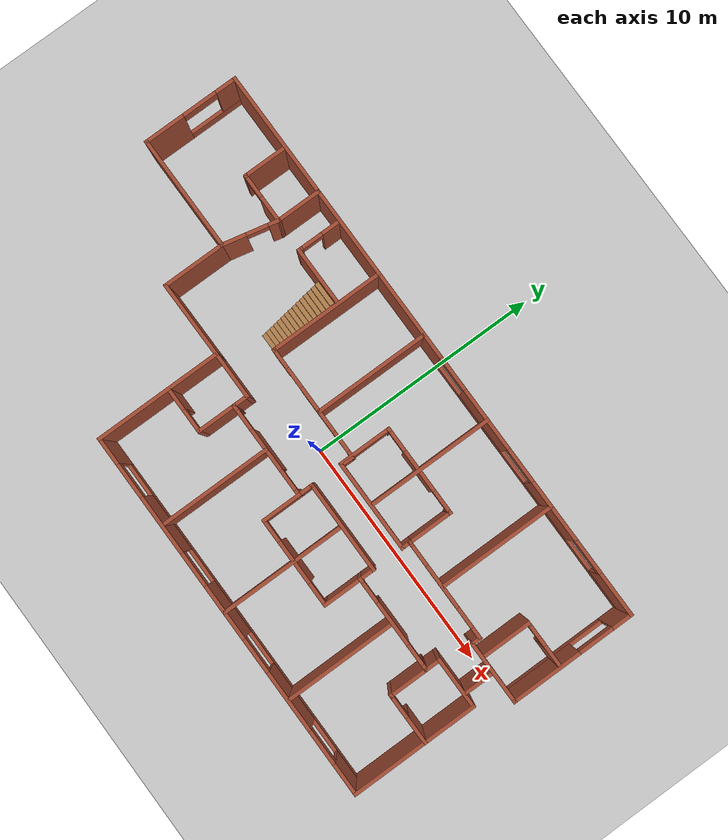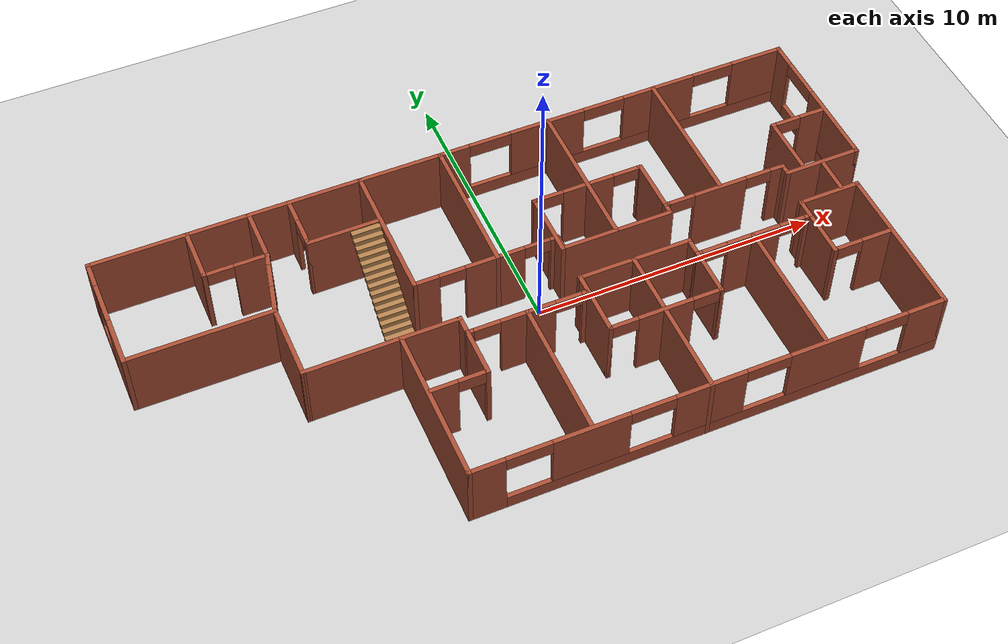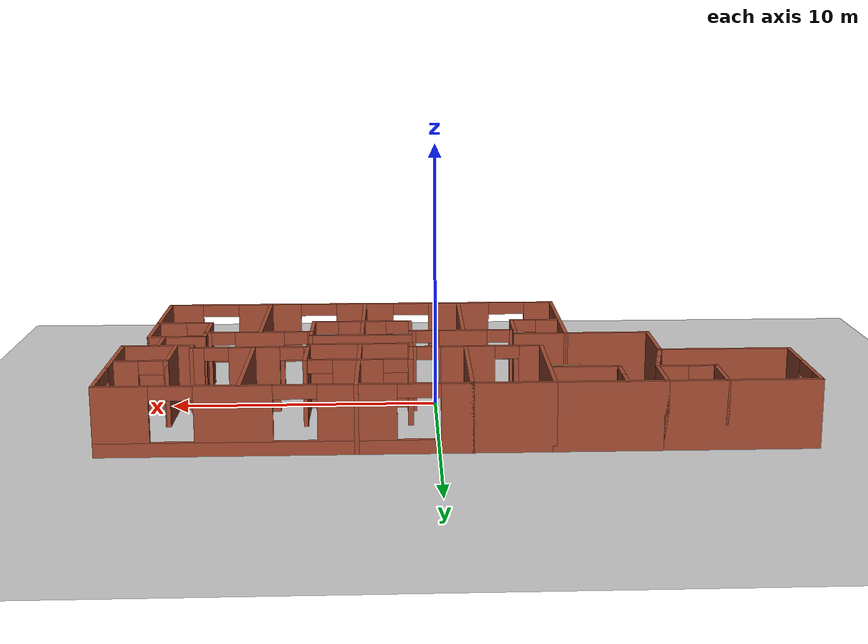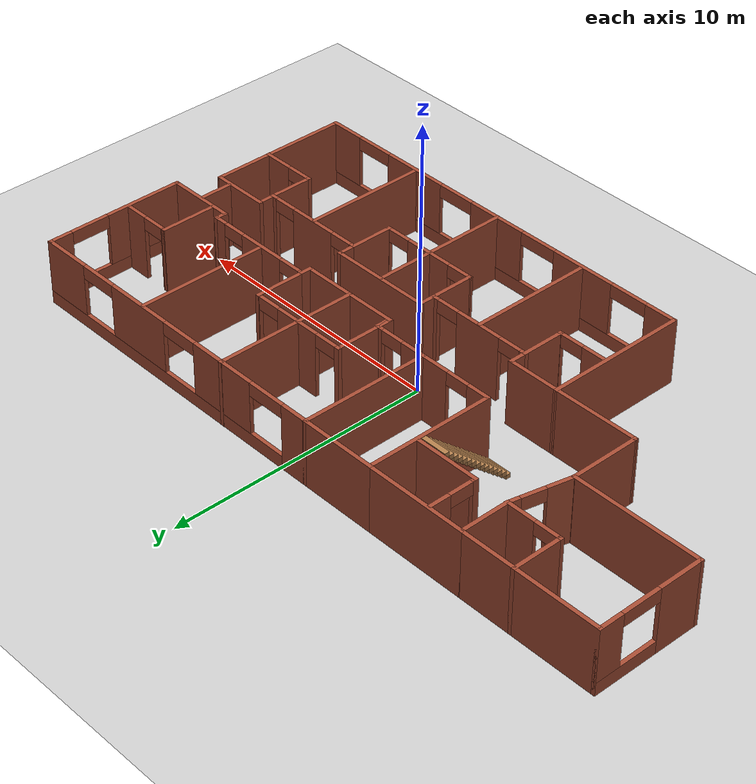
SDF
<sdf version="1.7">
 <world name="default">
  <light name="sun" type="directional">
   <pose>0 0 10 0 -0 0</pose>
   <diffuse>0.8 0.8 0.8 1</diffuse>
   <specular>0.2 0.2 0.2 1</specular>
   <attenuation>
    <range>1000</range>
    <constant>0.9</constant>
    <linear>0.01</linear>
    <quadratic>0.001</quadratic>
   </attenuation>
   <direction>-0.5 0.1 -0.9</direction>
   <spot><inner_angle>0</inner_angle><outer_angle>0</outer_angle><falloff>0</falloff></spot>
  </light>
  <model name="ground_plane">
   <static>1</static>
   <link name="link">
    <collision name="collision">
     <geometry><plane><normal>0 0 1</normal><size>100 100</size></plane></geometry>
     <surface><friction><ode><mu>100</mu><mu2>50</mu2></ode></friction></surface>
    </collision>
    <visual name="visual">
     <cast_shadows>0</cast_shadows>
     <geometry><plane><normal>0 0 1</normal><size>100 100</size></plane></geometry>
     <material>
      <script><uri>file://media/materials/scripts/gazebo.material</uri><name>Gazebo/Grey</name></script>
     </material>
    </visual>
   </link>
  </model>
  <gravity>0 0 -9.8</gravity>
  <magnetic_field>6e-06 2.3e-05 -4.2e-05</magnetic_field>
  <atmosphere type="adiabatic"/>
  <physics type="ode">
   <max_step_size>0.001</max_step_size>
   <real_time_factor>1</real_time_factor>
   <real_time_update_rate>1000</real_time_update_rate>
  </physics>
  <scene><ambient>0.4 0.4 0.4 1</ambient><background>0.7 0.7 0.7 1</background><shadows>1</shadows></scene>
  <audio><device>default</device></audio>
  <spherical_coordinates>
   <surface_model>EARTH_WGS84</surface_model>
   <latitude_deg>0</latitude_deg>
   <longitude_deg>0</longitude_deg>
   <elevation>0</elevation>
   <heading_deg>0</heading_deg>
  </spherical_coordinates>
  <model name="Apartments2">
   <pose>-0.710579 -0.305207 0 0 -0 0</pose>
   <link name="Stairs_0">
    <visual name="Stairs_0_Visual_0">
     <pose>-3.83768 1.22984 0.083333 0 -0 -3.14159</pose>
     <geometry><box><size>1 0.191726 0.166667</size></box></geometry>
     <material>
      <script><uri>file://media/materials/scripts/gazebo.material</uri><name>Gazebo/Wood</name></script>
      <ambient>1 1 1 1</ambient>
     </material>
     <meta><layer>0</layer></meta>
    </visual>
    <collision name="Stairs_0_Collision_0">
     <geometry><box><size>1 0.191726 0.166667</size></box></geometry>
     <pose>-3.83768 1.22984 0.083333 0 -0 -3.14159</pose>
    </collision>
    <visual name="Stairs_0_Visual_1">
     <pose>-3.83768 1.42156 0.25 0 -0 -3.14159</pose>
     <geometry><box><size>1 0.191726 0.166667</size></box></geometry>
     <material>
      <script><uri>file://media/materials/scripts/gazebo.material</uri><name>Gazebo/Wood</name></script>
      <ambient>1 1 1 1</ambient>
     </material>
     <meta><layer>0</layer></meta>
    </visual>
    <collision name="Stairs_0_Collision_1">
     <geometry><box><size>1 0.191726 0.166667</size></box></geometry>
     <pose>-3.83768 1.42156 0.25 0 -0 -3.14159</pose>
    </collision>
    <visual name="Stairs_0_Visual_2">
     <pose>-3.83768 1.61329 0.416667 0 -0 -3.14159</pose>
     <geometry><box><size>1 0.191726 0.166667</size></box></geometry>
     <material>
      <script><uri>file://media/materials/scripts/gazebo.material</uri><name>Gazebo/Wood</name></script>
      <ambient>1 1 1 1</ambient>
     </material>
     <meta><layer>0</layer></meta>
    </visual>
    <collision name="Stairs_0_Collision_2">
     <geometry><box><size>1 0.191726 0.166667</size></box></geometry>
     <pose>-3.83768 1.61329 0.416667 0 -0 -3.14159</pose>
    </collision>
    <visual name="Stairs_0_Visual_3">
     <pose>-3.83768 1.80502 0.583333 0 -0 -3.14159</pose>
     <geometry><box><size>1 0.191726 0.166667</size></box></geometry>
     <material>
      <script><uri>file://media/materials/scripts/gazebo.material</uri><name>Gazebo/Wood</name></script>
      <ambient>1 1 1 1</ambient>
     </material>
     <meta><layer>0</layer></meta>
    </visual>
    <collision name="Stairs_0_Collision_3">
     <geometry><box><size>1 0.191726 0.166667</size></box></geometry>
     <pose>-3.83768 1.80502 0.583333 0 -0 -3.14159</pose>
    </collision>
    <visual name="Stairs_0_Visual_4">
     <pose>-3.83768 1.99674 0.75 0 -0 -3.14159</pose>
     <geometry><box><size>1 0.191726 0.166667</size></box></geometry>
     <material>
      <script><uri>file://media/materials/scripts/gazebo.material</uri><name>Gazebo/Wood</name></script>
      <ambient>1 1 1 1</ambient>
     </material>
     <meta><layer>0</layer></meta>
    </visual>
    <collision name="Stairs_0_Collision_4">
     <geometry><box><size>1 0.191726 0.166667</size></box></geometry>
     <pose>-3.83768 1.99674 0.75 0 -0 -3.14159</pose>
    </collision>
    <visual name="Stairs_0_Visual_5">
     <pose>-3.83768 2.18847 0.916667 0 -0 -3.14159</pose>
     <geometry><box><size>1 0.191726 0.166667</size></box></geometry>
     <material>
      <script><uri>file://media/materials/scripts/gazebo.material</uri><name>Gazebo/Wood</name></script>
      <ambient>1 1 1 1</ambient>
     </material>
     <meta><layer>0</layer></meta>
    </visual>
    <collision name="Stairs_0_Collision_5">
     <geometry><box><size>1 0.191726 0.166667</size></box></geometry>
     <pose>-3.83768 2.18847 0.916667 0 -0 -3.14159</pose>
    </collision>
    <visual name="Stairs_0_Visual_6">
     <pose>-3.83768 2.38019 1.08333 0 -0 -3.14159</pose>
     <geometry><box><size>1 0.191726 0.166667</size></box></geometry>
     <material>
      <script><uri>file://media/materials/scripts/gazebo.material</uri><name>Gazebo/Wood</name></script>
      <ambient>1 1 1 1</ambient>
     </material>
     <meta><layer>0</layer></meta>
    </visual>
    <collision name="Stairs_0_Collision_6">
     <geometry><box><size>1 0.191726 0.166667</size></box></geometry>
     <pose>-3.83768 2.38019 1.08333 0 -0 -3.14159</pose>
    </collision>
    <visual name="Stairs_0_Visual_7">
     <pose>-3.83768 2.57192 1.25 0 -0 -3.14159</pose>
     <geometry><box><size>1 0.191726 0.166667</size></box></geometry>
     <material>
      <script><uri>file://media/materials/scripts/gazebo.material</uri><name>Gazebo/Wood</name></script>
      <ambient>1 1 1 1</ambient>
     </material>
     <meta><layer>0</layer></meta>
    </visual>
    <collision name="Stairs_0_Collision_7">
     <geometry><box><size>1 0.191726 0.166667</size></box></geometry>
     <pose>-3.83768 2.57192 1.25 0 -0 -3.14159</pose>
    </collision>
    <visual name="Stairs_0_Visual_8">
     <pose>-3.83768 2.76365 1.41667 0 -0 -3.14159</pose>
     <geometry><box><size>1 0.191726 0.166667</size></box></geometry>
     <material>
      <script><uri>file://media/materials/scripts/gazebo.material</uri><name>Gazebo/Wood</name></script>
      <ambient>1 1 1 1</ambient>
     </material>
     <meta><layer>0</layer></meta>
    </visual>
    <collision name="Stairs_0_Collision_8">
     <geometry><box><size>1 0.191726 0.166667</size></box></geometry>
     <pose>-3.83768 2.76365 1.41667 0 -0 -3.14159</pose>
    </collision>
    <visual name="Stairs_0_Visual_9">
     <pose>-3.83768 2.95537 1.58333 0 -0 -3.14159</pose>
     <geometry><box><size>1 0.191726 0.166667</size></box></geometry>
     <material>
      <script><uri>file://media/materials/scripts/gazebo.material</uri><name>Gazebo/Wood</name></script>
      <ambient>1 1 1 1</ambient>
     </material>
     <meta><layer>0</layer></meta>
    </visual>
    <collision name="Stairs_0_Collision_9">
     <geometry><box><size>1 0.191726 0.166667</size></box></geometry>
     <pose>-3.83768 2.95537 1.58333 0 -0 -3.14159</pose>
    </collision>
    <visual name="Stairs_0_Visual_10">
     <pose>-3.83768 3.1471 1.75 0 -0 -3.14159</pose>
     <geometry><box><size>1 0.191726 0.166667</size></box></geometry>
     <material>
      <script><uri>file://media/materials/scripts/gazebo.material</uri><name>Gazebo/Wood</name></script>
      <ambient>1 1 1 1</ambient>
     </material>
     <meta><layer>0</layer></meta>
    </visual>
    <collision name="Stairs_0_Collision_10">
     <geometry><box><size>1 0.191726 0.166667</size></box></geometry>
     <pose>-3.83768 3.1471 1.75 0 -0 -3.14159</pose>
    </collision>
    <visual name="Stairs_0_Visual_11">
     <pose>-3.83768 3.33882 1.91667 0 -0 -3.14159</pose>
     <geometry><box><size>1 0.191726 0.166667</size></box></geometry>
     <material>
      <script><uri>file://media/materials/scripts/gazebo.material</uri><name>Gazebo/Wood</name></script>
      <ambient>1 1 1 1</ambient>
     </material>
     <meta><layer>0</layer></meta>
    </visual>
    <collision name="Stairs_0_Collision_11">
     <geometry><box><size>1 0.191726 0.166667</size></box></geometry>
     <pose>-3.83768 3.33882 1.91667 0 -0 -3.14159</pose>
    </collision>
    <visual name="Stairs_0_Visual_12">
     <pose>-3.83768 3.53055 2.08333 0 -0 -3.14159</pose>
     <geometry><box><size>1 0.191726 0.166667</size></box></geometry>
     <material>
      <script><uri>file://media/materials/scripts/gazebo.material</uri><name>Gazebo/Wood</name></script>
      <ambient>1 1 1 1</ambient>
     </material>
     <meta><layer>0</layer></meta>
    </visual>
    <collision name="Stairs_0_Collision_12">
     <geometry><box><size>1 0.191726 0.166667</size></box></geometry>
     <pose>-3.83768 3.53055 2.08333 0 -0 -3.14159</pose>
    </collision>
    <visual name="Stairs_0_Visual_13">
     <pose>-3.83768 3.72228 2.25 0 -0 -3.14159</pose>
     <geometry><box><size>1 0.191726 0.166667</size></box></geometry>
     <material>
      <script><uri>file://media/materials/scripts/gazebo.material</uri><name>Gazebo/Wood</name></script>
      <ambient>1 1 1 1</ambient>
     </material>
     <meta><layer>0</layer></meta>
    </visual>
    <collision name="Stairs_0_Collision_13">
     <geometry><box><size>1 0.191726 0.166667</size></box></geometry>
     <pose>-3.83768 3.72228 2.25 0 -0 -3.14159</pose>
    </collision>
    <visual name="Stairs_0_Visual_14">
     <pose>-3.83768 3.914 2.41667 0 -0 -3.14159</pose>
     <geometry><box><size>1 0.191726 0.166667</size></box></geometry>
     <material>
      <script><uri>file://media/materials/scripts/gazebo.material</uri><name>Gazebo/Wood</name></script>
      <ambient>1 1 1 1</ambient>
     </material>
     <meta><layer>0</layer></meta>
    </visual>
    <collision name="Stairs_0_Collision_14">
     <geometry><box><size>1 0.191726 0.166667</size></box></geometry>
     <pose>-3.83768 3.914 2.41667 0 -0 -3.14159</pose>
    </collision>
   </link>
   <link name="Wall_100">
    <collision name="Wall_100_Collision">
     <geometry><box><size>1.25 0.15 2.5</size></box></geometry>
     <pose>0 0 1.25 0 -0 0</pose>
    </collision>
    <visual name="Wall_100_Visual">
     <pose>0 0 1.25 0 -0 0</pose>
     <geometry><box><size>1.25 0.15 2.5</size></box></geometry>
     <material>
      <script><uri>file://media/materials/scripts/gazebo.material</uri><name>Gazebo/Bricks</name></script>
      <ambient>1 1 1 1</ambient>
     </material>
     <meta><layer>0</layer></meta>
    </visual>
    <pose>11.1408 -0.014942 0 0 -0 1.5708</pose>
   </link>
   <link name="Wall_105">
    <collision name="Wall_105_Collision">
     <geometry><box><size>1.75 0.15 2.5</size></box></geometry>
     <pose>0 0 1.25 0 -0 0</pose>
    </collision>
    <visual name="Wall_105_Visual">
     <pose>0 0 1.25 0 -0 0</pose>
     <geometry><box><size>1.75 0.15 2.5</size></box></geometry>
     <material>
      <script><uri>file://media/materials/scripts/gazebo.material</uri><name>Gazebo/Bricks</name></script>
      <ambient>1 1 1 1</ambient>
     </material>
     <meta><layer>0</layer></meta>
    </visual>
    <pose>-2.44477 -2.06693 0 0 -0 -1.5708</pose>
   </link>
   <link name="Wall_106">
    <pose>-3.36977 -2.86693 0 0 -0 3.14159</pose>
    <visual name="Wall_106_Visual_0">
     <pose>-0.920669 0 1.25 0 -0 0</pose>
     <geometry><box><size>0.158663 0.15 2.5</size></box></geometry>
     <material>
      <script><uri>file://media/materials/scripts/gazebo.material</uri><name>Gazebo/Bricks</name></script>
      <ambient>1 1 1 1</ambient>
     </material>
     <meta><layer>0</layer></meta>
    </visual>
    <collision name="Wall_106_Collision_0">
     <geometry><box><size>0.158663 0.15 2.5</size></box></geometry>
     <pose>-0.920669 0 1.25 0 -0 0</pose>
    </collision>
    <visual name="Wall_106_Visual_1">
     <pose>0.529331 0 1.25 0 -0 0</pose>
     <geometry><box><size>0.941337 0.15 2.5</size></box></geometry>
     <material>
      <script><uri>file://media/materials/scripts/gazebo.material</uri><name>Gazebo/Bricks</name></script>
      <ambient>1 1 1 1</ambient>
     </material>
     <meta><layer>0</layer></meta>
    </visual>
    <collision name="Wall_106_Collision_1">
     <geometry><box><size>0.941337 0.15 2.5</size></box></geometry>
     <pose>0.529331 0 1.25 0 -0 0</pose>
    </collision>
    <visual name="Wall_106_Visual_2">
     <pose>-0.391337 0 2.25 0 -0 0</pose>
     <geometry><box><size>0.9 0.15 0.5</size></box></geometry>
     <material>
      <script><uri>file://media/materials/scripts/gazebo.material</uri><name>Gazebo/Bricks</name></script>
      <ambient>1 1 1 1</ambient>
     </material>
     <meta><layer>0</layer></meta>
    </visual>
    <collision name="Wall_106_Collision_2">
     <geometry><box><size>0.9 0.15 0.5</size></box></geometry>
     <pose>-0.391337 0 2.25 0 -0 0</pose>
    </collision>
   </link>
   <link name="Wall_14">
    <pose>-7.35 3.03684 0 0 -0 1.35213</pose>
    <visual name="Wall_14_Visual_0">
     <pose>-0.699604 0 1.25 0 -0 0</pose>
     <geometry><box><size>1.05568 0.15 2.5</size></box></geometry>
     <material>
      <script><uri>file://media/materials/scripts/gazebo.material</uri><name>Gazebo/Bricks</name></script>
      <ambient>1 1 1 1</ambient>
     </material>
     <meta><layer>0</layer></meta>
    </visual>
    <collision name="Wall_14_Collision_0">
     <geometry><box><size>1.05568 0.15 2.5</size></box></geometry>
     <pose>-0.699604 0 1.25 0 -0 0</pose>
    </collision>
    <visual name="Wall_14_Visual_1">
     <pose>0.977839 0 1.25 0 -0 0</pose>
     <geometry><box><size>0.499209 0.15 2.5</size></box></geometry>
     <material>
      <script><uri>file://media/materials/scripts/gazebo.material</uri><name>Gazebo/Bricks</name></script>
      <ambient>1 1 1 1</ambient>
     </material>
     <meta><layer>0</layer></meta>
    </visual>
    <collision name="Wall_14_Collision_1">
     <geometry><box><size>0.499209 0.15 2.5</size></box></geometry>
     <pose>0.977839 0 1.25 0 -0 0</pose>
    </collision>
    <visual name="Wall_14_Visual_2">
     <pose>0.278234 0 2.25 0 -0 0</pose>
     <geometry><box><size>0.9 0.15 0.5</size></box></geometry>
     <material>
      <script><uri>file://media/materials/scripts/gazebo.material</uri><name>Gazebo/Bricks</name></script>
      <ambient>1 1 1 1</ambient>
     </material>
     <meta><layer>0</layer></meta>
    </visual>
    <collision name="Wall_14_Collision_2">
     <geometry><box><size>0.9 0.15 0.5</size></box></geometry>
     <pose>0.278234 0 2.25 0 -0 0</pose>
    </collision>
   </link>
   <link name="Wall_16">
    <collision name="Wall_16_Collision">
     <geometry><box><size>5.5 0.15 2.5</size></box></geometry>
     <pose>0 0 1.25 0 -0 0</pose>
    </collision>
    <visual name="Wall_16_Visual">
     <pose>0 0 1.25 0 -0 0</pose>
     <geometry><box><size>5.5 0.15 2.5</size></box></geometry>
     <material>
      <script><uri>file://media/materials/scripts/gazebo.material</uri><name>Gazebo/Bricks</name></script>
      <ambient>1 1 1 1</ambient>
     </material>
     <meta><layer>0</layer></meta>
    </visual>
    <pose>-4.39477 -3.34193 0 0 -0 -1.5708</pose>
   </link>
   <link name="Wall_17">
    <pose>3.65523 -6.01693 0 0 -0 0</pose>
    <visual name="Wall_17_Visual_0">
     <pose>-7.50207 0 1.25 0 -0 0</pose>
     <geometry><box><size>1.24587 0.15 2.5</size></box></geometry>
     <material>
      <script><uri>file://media/materials/scripts/gazebo.material</uri><name>Gazebo/Bricks</name></script>
      <ambient>1 1 1 1</ambient>
     </material>
     <meta><layer>0</layer></meta>
    </visual>
    <collision name="Wall_17_Collision_0">
     <geometry><box><size>1.24587 0.15 2.5</size></box></geometry>
     <pose>-7.50207 0 1.25 0 -0 0</pose>
    </collision>
    <visual name="Wall_17_Visual_1">
     <pose>0.622932 0 0.25 0 -0 0</pose>
     <geometry><box><size>15.0041 0.15 0.5</size></box></geometry>
     <material>
      <script><uri>file://media/materials/scripts/gazebo.material</uri><name>Gazebo/Bricks</name></script>
      <ambient>1 1 1 1</ambient>
     </material>
     <meta><layer>0</layer></meta>
    </visual>
    <collision name="Wall_17_Collision_1">
     <geometry><box><size>15.0041 0.15 0.5</size></box></geometry>
     <pose>0.622932 0 0.25 0 -0 0</pose>
    </collision>
    <visual name="Wall_17_Visual_2">
     <pose>-4.09785 0 1.5 0 -0 0</pose>
     <geometry><box><size>2.56257 0.15 2</size></box></geometry>
     <material>
      <script><uri>file://media/materials/scripts/gazebo.material</uri><name>Gazebo/Bricks</name></script>
      <ambient>1 1 1 1</ambient>
     </material>
     <meta><layer>0</layer></meta>
    </visual>
    <collision name="Wall_17_Collision_2">
     <geometry><box><size>2.56257 0.15 2</size></box></geometry>
     <pose>-4.09785 0 1.5 0 -0 0</pose>
    </collision>
    <visual name="Wall_17_Visual_3">
     <pose>-0.113307 0 1.5 0 -0 0</pose>
     <geometry><box><size>2.40652 0.15 2</size></box></geometry>
     <material>
      <script><uri>file://media/materials/scripts/gazebo.material</uri><name>Gazebo/Bricks</name></script>
      <ambient>1 1 1 1</ambient>
     </material>
     <meta><layer>0</layer></meta>
    </visual>
    <collision name="Wall_17_Collision_3">
     <geometry><box><size>2.40652 0.15 2</size></box></geometry>
     <pose>-0.113307 0 1.5 0 -0 0</pose>
    </collision>
    <visual name="Wall_17_Visual_4">
     <pose>3.90561 0 1.5 0 -0 0</pose>
     <geometry><box><size>2.63132 0.15 2</size></box></geometry>
     <material>
      <script><uri>file://media/materials/scripts/gazebo.material</uri><name>Gazebo/Bricks</name></script>
      <ambient>1 1 1 1</ambient>
     </material>
     <meta><layer>0</layer></meta>
    </visual>
    <collision name="Wall_17_Collision_4">
     <geometry><box><size>2.63132 0.15 2</size></box></geometry>
     <pose>3.90561 0 1.5 0 -0 0</pose>
    </collision>
    <visual name="Wall_17_Visual_5">
     <pose>7.42314 0 1.5 0 -0 0</pose>
     <geometry><box><size>1.40373 0.15 2</size></box></geometry>
     <material>
      <script><uri>file://media/materials/scripts/gazebo.material</uri><name>Gazebo/Bricks</name></script>
      <ambient>1 1 1 1</ambient>
     </material>
     <meta><layer>0</layer></meta>
    </visual>
    <collision name="Wall_17_Collision_5">
     <geometry><box><size>1.40373 0.15 2</size></box></geometry>
     <pose>7.42314 0 1.5 0 -0 0</pose>
    </collision>
    <visual name="Wall_17_Visual_6">
     <pose>-6.12913 0 2.25 0 -0 0</pose>
     <geometry><box><size>1.5 0.15 0.5</size></box></geometry>
     <material>
      <script><uri>file://media/materials/scripts/gazebo.material</uri><name>Gazebo/Bricks</name></script>
      <ambient>1 1 1 1</ambient>
     </material>
     <meta><layer>0</layer></meta>
    </visual>
    <collision name="Wall_17_Collision_6">
     <geometry><box><size>1.5 0.15 0.5</size></box></geometry>
     <pose>-6.12913 0 2.25 0 -0 0</pose>
    </collision>
    <visual name="Wall_17_Visual_7">
     <pose>-2.06656 0 2.25 0 -0 0</pose>
     <geometry><box><size>1.5 0.15 0.5</size></box></geometry>
     <material>
      <script><uri>file://media/materials/scripts/gazebo.material</uri><name>Gazebo/Bricks</name></script>
      <ambient>1 1 1 1</ambient>
     </material>
     <meta><layer>0</layer></meta>
    </visual>
    <collision name="Wall_17_Collision_7">
     <geometry><box><size>1.5 0.15 0.5</size></box></geometry>
     <pose>-2.06656 0 2.25 0 -0 0</pose>
    </collision>
    <visual name="Wall_17_Visual_8">
     <pose>1.83995 0 2.25 0 -0 0</pose>
     <geometry><box><size>1.5 0.15 0.5</size></box></geometry>
     <material>
      <script><uri>file://media/materials/scripts/gazebo.material</uri><name>Gazebo/Bricks</name></script>
      <ambient>1 1 1 1</ambient>
     </material>
     <meta><layer>0</layer></meta>
    </visual>
    <collision name="Wall_17_Collision_8">
     <geometry><box><size>1.5 0.15 0.5</size></box></geometry>
     <pose>1.83995 0 2.25 0 -0 0</pose>
    </collision>
    <visual name="Wall_17_Visual_9">
     <pose>5.97127 0 2.25 0 -0 0</pose>
     <geometry><box><size>1.5 0.15 0.5</size></box></geometry>
     <material>
      <script><uri>file://media/materials/scripts/gazebo.material</uri><name>Gazebo/Bricks</name></script>
      <ambient>1 1 1 1</ambient>
     </material>
     <meta><layer>0</layer></meta>
    </visual>
    <collision name="Wall_17_Collision_9">
     <geometry><box><size>1.5 0.15 0.5</size></box></geometry>
     <pose>5.97127 0 2.25 0 -0 0</pose>
    </collision>
   </link>
   <link name="Wall_18">
    <collision name="Wall_18_Collision">
     <geometry><box><size>5.5 0.15 2.5</size></box></geometry>
     <pose>0 0 1.25 0 -0 0</pose>
    </collision>
    <visual name="Wall_18_Visual">
     <pose>0 0 1.25 0 -0 0</pose>
     <geometry><box><size>5.5 0.15 2.5</size></box></geometry>
     <material>
      <script><uri>file://media/materials/scripts/gazebo.material</uri><name>Gazebo/Bricks</name></script>
      <ambient>1 1 1 1</ambient>
     </material>
     <meta><layer>0</layer></meta>
    </visual>
    <pose>11.7052 -3.34193 0 0 -0 1.5708</pose>
   </link>
   <link name="Wall_19">
    <collision name="Wall_19_Collision">
     <geometry><box><size>2.25 0.15 2.5</size></box></geometry>
     <pose>0 0 1.25 0 -0 0</pose>
    </collision>
    <visual name="Wall_19_Visual">
     <pose>0 0 1.25 0 -0 0</pose>
     <geometry><box><size>2.25 0.15 2.5</size></box></geometry>
     <material>
      <script><uri>file://media/materials/scripts/gazebo.material</uri><name>Gazebo/Bricks</name></script>
      <ambient>1 1 1 1</ambient>
     </material>
     <meta><layer>0</layer></meta>
    </visual>
    <pose>10.6552 -0.666927 0 0 -0 3.14159</pose>
   </link>
   <link name="Wall_2">
    <collision name="Wall_2_Collision">
     <geometry><box><size>5 0.15 2.5</size></box></geometry>
     <pose>0 0 1.25 0 -0 0</pose>
    </collision>
    <visual name="Wall_2_Visual">
     <pose>0 0 1.25 0 -0 0</pose>
     <geometry><box><size>5 0.15 2.5</size></box></geometry>
     <material>
      <script><uri>file://media/materials/scripts/gazebo.material</uri><name>Gazebo/Bricks</name></script>
      <ambient>1 1 1 1</ambient>
     </material>
     <meta><layer>0</layer></meta>
    </visual>
    <pose>-10.025 1.91184 0 0 -0 3.14159</pose>
   </link>
   <link name="Wall_20">
    <collision name="Wall_20_Collision">
     <geometry><box><size>0.75 0.15 2.5</size></box></geometry>
     <pose>0 0 1.25 0 -0 0</pose>
    </collision>
    <visual name="Wall_20_Visual">
     <pose>0 0 1.25 0 -0 0</pose>
     <geometry><box><size>0.75 0.15 2.5</size></box></geometry>
     <material>
      <script><uri>file://media/materials/scripts/gazebo.material</uri><name>Gazebo/Bricks</name></script>
      <ambient>1 1 1 1</ambient>
     </material>
     <meta><layer>0</layer></meta>
    </visual>
    <pose>9.60523 -0.966927 0 0 -0 -1.5708</pose>
   </link>
   <link name="Wall_21">
    <pose>7.55523 -1.26693 0 0 -0 3.14159</pose>
    <visual name="Wall_21_Visual_0">
     <pose>-1.97774 0 1.25 0 -0 0</pose>
     <geometry><box><size>0.294523 0.15 2.5</size></box></geometry>
     <material>
      <script><uri>file://media/materials/scripts/gazebo.material</uri><name>Gazebo/Bricks</name></script>
      <ambient>1 1 1 1</ambient>
     </material>
     <meta><layer>0</layer></meta>
    </visual>
    <collision name="Wall_21_Collision_0">
     <geometry><box><size>0.294523 0.15 2.5</size></box></geometry>
     <pose>-1.97774 0 1.25 0 -0 0</pose>
    </collision>
    <visual name="Wall_21_Visual_1">
     <pose>0.028428 0 1.25 0 -0 0</pose>
     <geometry><box><size>1.91781 0.15 2.5</size></box></geometry>
     <material>
      <script><uri>file://media/materials/scripts/gazebo.material</uri><name>Gazebo/Bricks</name></script>
      <ambient>1 1 1 1</ambient>
     </material>
     <meta><layer>0</layer></meta>
    </visual>
    <collision name="Wall_21_Collision_1">
     <geometry><box><size>1.91781 0.15 2.5</size></box></geometry>
     <pose>0.028428 0 1.25 0 -0 0</pose>
    </collision>
    <visual name="Wall_21_Visual_2">
     <pose>2.00617 0 1.25 0 -0 0</pose>
     <geometry><box><size>0.237667 0.15 2.5</size></box></geometry>
     <material>
      <script><uri>file://media/materials/scripts/gazebo.material</uri><name>Gazebo/Bricks</name></script>
      <ambient>1 1 1 1</ambient>
     </material>
     <meta><layer>0</layer></meta>
    </visual>
    <collision name="Wall_21_Collision_2">
     <geometry><box><size>0.237667 0.15 2.5</size></box></geometry>
     <pose>2.00617 0 1.25 0 -0 0</pose>
    </collision>
    <visual name="Wall_21_Visual_3">
     <pose>-1.38048 0 2.25 0 -0 0</pose>
     <geometry><box><size>0.9 0.15 0.5</size></box></geometry>
     <material>
      <script><uri>file://media/materials/scripts/gazebo.material</uri><name>Gazebo/Bricks</name></script>
      <ambient>1 1 1 1</ambient>
     </material>
     <meta><layer>0</layer></meta>
    </visual>
    <collision name="Wall_21_Collision_3">
     <geometry><box><size>0.9 0.15 0.5</size></box></geometry>
     <pose>-1.38048 0 2.25 0 -0 0</pose>
    </collision>
    <visual name="Wall_21_Visual_4">
     <pose>1.43733 0 2.25 0 -0 0</pose>
     <geometry><box><size>0.9 0.15 0.5</size></box></geometry>
     <material>
      <script><uri>file://media/materials/scripts/gazebo.material</uri><name>Gazebo/Bricks</name></script>
      <ambient>1 1 1 1</ambient>
     </material>
     <meta><layer>0</layer></meta>
    </visual>
    <collision name="Wall_21_Collision_4">
     <geometry><box><size>0.9 0.15 0.5</size></box></geometry>
     <pose>1.43733 0 2.25 0 -0 0</pose>
    </collision>
   </link>
   <link name="Wall_22">
    <collision name="Wall_22_Collision">
     <geometry><box><size>0.75 0.15 2.5</size></box></geometry>
     <pose>0 0 1.25 0 -0 0</pose>
    </collision>
    <visual name="Wall_22_Visual">
     <pose>0 0 1.25 0 -0 0</pose>
     <geometry><box><size>0.75 0.15 2.5</size></box></geometry>
     <material>
      <script><uri>file://media/materials/scripts/gazebo.material</uri><name>Gazebo/Bricks</name></script>
      <ambient>1 1 1 1</ambient>
     </material>
     <meta><layer>0</layer></meta>
    </visual>
    <pose>5.50523 -0.966927 0 0 -0 1.5708</pose>
   </link>
   <link name="Wall_23">
    <collision name="Wall_23_Collision">
     <geometry><box><size>4 0.15 2.5</size></box></geometry>
     <pose>0 0 1.25 0 -0 0</pose>
    </collision>
    <visual name="Wall_23_Visual">
     <pose>0 0 1.25 0 -0 0</pose>
     <geometry><box><size>4 0.15 2.5</size></box></geometry>
     <material>
      <script><uri>file://media/materials/scripts/gazebo.material</uri><name>Gazebo/Bricks</name></script>
      <ambient>1 1 1 1</ambient>
     </material>
     <meta><layer>0</layer></meta>
    </visual>
    <pose>3.58023 -0.666927 0 0 -0 3.14159</pose>
   </link>
   <link name="Wall_24">
    <collision name="Wall_24_Collision">
     <geometry><box><size>0.75 0.15 2.5</size></box></geometry>
     <pose>0 0 1.25 0 -0 0</pose>
    </collision>
    <visual name="Wall_24_Visual">
     <pose>0 0 1.25 0 -0 0</pose>
     <geometry><box><size>0.75 0.15 2.5</size></box></geometry>
     <material>
      <script><uri>file://media/materials/scripts/gazebo.material</uri><name>Gazebo/Bricks</name></script>
      <ambient>1 1 1 1</ambient>
     </material>
     <meta><layer>0</layer></meta>
    </visual>
    <pose>1.65523 -0.966927 0 0 -0 -1.5708</pose>
   </link>
   <link name="Wall_25">
    <pose>-0.394772 -1.26693 0 0 -0 3.14159</pose>
    <visual name="Wall_25_Visual_0">
     <pose>-1.97566 0 1.25 0 -0 0</pose>
     <geometry><box><size>0.298682 0.15 2.5</size></box></geometry>
     <material>
      <script><uri>file://media/materials/scripts/gazebo.material</uri><name>Gazebo/Bricks</name></script>
      <ambient>1 1 1 1</ambient>
     </material>
     <meta><layer>0</layer></meta>
    </visual>
    <collision name="Wall_25_Collision_0">
     <geometry><box><size>0.298682 0.15 2.5</size></box></geometry>
     <pose>-1.97566 0 1.25 0 -0 0</pose>
    </collision>
    <visual name="Wall_25_Visual_1">
     <pose>0.012069 0 1.25 0 -0 0</pose>
     <geometry><box><size>1.87677 0.15 2.5</size></box></geometry>
     <material>
      <script><uri>file://media/materials/scripts/gazebo.material</uri><name>Gazebo/Bricks</name></script>
      <ambient>1 1 1 1</ambient>
     </material>
     <meta><layer>0</layer></meta>
    </visual>
    <collision name="Wall_25_Collision_1">
     <geometry><box><size>1.87677 0.15 2.5</size></box></geometry>
     <pose>0.012069 0 1.25 0 -0 0</pose>
    </collision>
    <visual name="Wall_25_Visual_2">
     <pose>1.98773 0 1.25 0 -0 0</pose>
     <geometry><box><size>0.274544 0.15 2.5</size></box></geometry>
     <material>
      <script><uri>file://media/materials/scripts/gazebo.material</uri><name>Gazebo/Bricks</name></script>
      <ambient>1 1 1 1</ambient>
     </material>
     <meta><layer>0</layer></meta>
    </visual>
    <collision name="Wall_25_Collision_2">
     <geometry><box><size>0.274544 0.15 2.5</size></box></geometry>
     <pose>1.98773 0 1.25 0 -0 0</pose>
    </collision>
    <visual name="Wall_25_Visual_3">
     <pose>-1.37632 0 2.25 0 -0 0</pose>
     <geometry><box><size>0.9 0.15 0.5</size></box></geometry>
     <material>
      <script><uri>file://media/materials/scripts/gazebo.material</uri><name>Gazebo/Bricks</name></script>
      <ambient>1 1 1 1</ambient>
     </material>
     <meta><layer>0</layer></meta>
    </visual>
    <collision name="Wall_25_Collision_3">
     <geometry><box><size>0.9 0.15 0.5</size></box></geometry>
     <pose>-1.37632 0 2.25 0 -0 0</pose>
    </collision>
    <visual name="Wall_25_Visual_4">
     <pose>1.40046 0 2.25 0 -0 0</pose>
     <geometry><box><size>0.9 0.15 0.5</size></box></geometry>
     <material>
      <script><uri>file://media/materials/scripts/gazebo.material</uri><name>Gazebo/Bricks</name></script>
      <ambient>1 1 1 1</ambient>
     </material>
     <meta><layer>0</layer></meta>
    </visual>
    <collision name="Wall_25_Collision_4">
     <geometry><box><size>0.9 0.15 0.5</size></box></geometry>
     <pose>1.40046 0 2.25 0 -0 0</pose>
    </collision>
   </link>
   <link name="Wall_26">
    <collision name="Wall_26_Collision">
     <geometry><box><size>0.75 0.15 2.5</size></box></geometry>
     <pose>0 0 1.25 0 -0 0</pose>
    </collision>
    <visual name="Wall_26_Visual">
     <pose>0 0 1.25 0 -0 0</pose>
     <geometry><box><size>0.75 0.15 2.5</size></box></geometry>
     <material>
      <script><uri>file://media/materials/scripts/gazebo.material</uri><name>Gazebo/Bricks</name></script>
      <ambient>1 1 1 1</ambient>
     </material>
     <meta><layer>0</layer></meta>
    </visual>
    <pose>-2.44477 -0.966927 0 0 -0 1.5708</pose>
   </link>
   <link name="Wall_27">
    <collision name="Wall_27_Collision">
     <geometry><box><size>2.1 0.15 2.5</size></box></geometry>
     <pose>0 0 1.25 0 -0 0</pose>
    </collision>
    <visual name="Wall_27_Visual">
     <pose>0 0 1.25 0 -0 0</pose>
     <geometry><box><size>2.1 0.15 2.5</size></box></geometry>
     <material>
      <script><uri>file://media/materials/scripts/gazebo.material</uri><name>Gazebo/Bricks</name></script>
      <ambient>1 1 1 1</ambient>
     </material>
     <meta><layer>0</layer></meta>
    </visual>
    <pose>-3.41977 -0.666927 0 0 -0 -3.14159</pose>
   </link>
   <link name="Wall_3">
    <pose>-12.45 3.96184 0 0 -0 1.5708</pose>
    <visual name="Wall_3_Visual_0">
     <pose>-1.23573 0 1.25 0 -0 0</pose>
     <geometry><box><size>1.77855 0.15 2.5</size></box></geometry>
     <material>
      <script><uri>file://media/materials/scripts/gazebo.material</uri><name>Gazebo/Bricks</name></script>
      <ambient>1 1 1 1</ambient>
     </material>
     <meta><layer>0</layer></meta>
    </visual>
    <collision name="Wall_3_Collision_0">
     <geometry><box><size>1.77855 0.15 2.5</size></box></geometry>
     <pose>-1.23573 0 1.25 0 -0 0</pose>
    </collision>
    <visual name="Wall_3_Visual_1">
     <pose>0.889273 0 0.25 0 -0 0</pose>
     <geometry><box><size>2.47145 0.15 0.5</size></box></geometry>
     <material>
      <script><uri>file://media/materials/scripts/gazebo.material</uri><name>Gazebo/Bricks</name></script>
      <ambient>1 1 1 1</ambient>
     </material>
     <meta><layer>0</layer></meta>
    </visual>
    <collision name="Wall_3_Collision_1">
     <geometry><box><size>2.47145 0.15 0.5</size></box></geometry>
     <pose>0.889273 0 0.25 0 -0 0</pose>
    </collision>
    <visual name="Wall_3_Visual_2">
     <pose>1.63927 0 1.5 0 -0 0</pose>
     <geometry><box><size>0.971454 0.15 2</size></box></geometry>
     <material>
      <script><uri>file://media/materials/scripts/gazebo.material</uri><name>Gazebo/Bricks</name></script>
      <ambient>1 1 1 1</ambient>
     </material>
     <meta><layer>0</layer></meta>
    </visual>
    <collision name="Wall_3_Collision_2">
     <geometry><box><size>0.971454 0.15 2</size></box></geometry>
     <pose>1.63927 0 1.5 0 -0 0</pose>
    </collision>
    <visual name="Wall_3_Visual_3">
     <pose>0.403546 0 2.25 0 -0 0</pose>
     <geometry><box><size>1.5 0.15 0.5</size></box></geometry>
     <material>
      <script><uri>file://media/materials/scripts/gazebo.material</uri><name>Gazebo/Bricks</name></script>
      <ambient>1 1 1 1</ambient>
     </material>
     <meta><layer>0</layer></meta>
    </visual>
    <collision name="Wall_3_Collision_3">
     <geometry><box><size>1.5 0.15 0.5</size></box></geometry>
     <pose>0.403546 0 2.25 0 -0 0</pose>
    </collision>
   </link>
   <link name="Wall_30">
    <collision name="Wall_30_Collision">
     <geometry><box><size>4.75 0.15 2.5</size></box></geometry>
     <pose>0 0 1.25 0 -0 0</pose>
    </collision>
    <visual name="Wall_30_Visual">
     <pose>0 0 1.25 0 -0 0</pose>
     <geometry><box><size>4.75 0.15 2.5</size></box></geometry>
     <material>
      <script><uri>file://media/materials/scripts/gazebo.material</uri><name>Gazebo/Bricks</name></script>
      <ambient>1 1 1 1</ambient>
     </material>
     <meta><layer>0</layer></meta>
    </visual>
    <pose>-0.419442 -3.57774 0 0 -0 -1.5708</pose>
   </link>
   <link name="Wall_35">
    <collision name="Wall_35_Collision">
     <geometry><box><size>5.5 0.15 2.5</size></box></geometry>
     <pose>0 0 1.25 0 -0 0</pose>
    </collision>
    <visual name="Wall_35_Visual">
     <pose>0 0 1.25 0 -0 0</pose>
     <geometry><box><size>5.5 0.15 2.5</size></box></geometry>
     <material>
      <script><uri>file://media/materials/scripts/gazebo.material</uri><name>Gazebo/Bricks</name></script>
      <ambient>1 1 1 1</ambient>
     </material>
     <meta><layer>0</layer></meta>
    </visual>
    <pose>3.53618 -3.34257 0 0 -0 -1.5708</pose>
   </link>
   <link name="Wall_37">
    <collision name="Wall_37_Collision">
     <geometry><box><size>4.75 0.15 2.5</size></box></geometry>
     <pose>0 0 1.25 0 -0 0</pose>
    </collision>
    <visual name="Wall_37_Visual">
     <pose>0 0 1.25 0 -0 0</pose>
     <geometry><box><size>4.75 0.15 2.5</size></box></geometry>
     <material>
      <script><uri>file://media/materials/scripts/gazebo.material</uri><name>Gazebo/Bricks</name></script>
      <ambient>1 1 1 1</ambient>
     </material>
     <meta><layer>0</layer></meta>
    </visual>
    <pose>7.51283 -3.59878 0 0 -0 -1.5708</pose>
   </link>
   <link name="Wall_4">
    <collision name="Wall_4_Collision">
     <geometry><box><size>5.5 0.15 2.5</size></box></geometry>
     <pose>0 0 1.25 0 -0 0</pose>
    </collision>
    <visual name="Wall_4_Visual">
     <pose>0 0 1.25 0 -0 0</pose>
     <geometry><box><size>5.5 0.15 2.5</size></box></geometry>
     <material>
      <script><uri>file://media/materials/scripts/gazebo.material</uri><name>Gazebo/Bricks</name></script>
      <ambient>1 1 1 1</ambient>
     </material>
     <meta><layer>0</layer></meta>
    </visual>
    <pose>-9.775 6.01184 0 0 -0 0</pose>
   </link>
   <link name="Wall_43">
    <collision name="Wall_43_Collision">
     <geometry><box><size>1.75 0.15 2.5</size></box></geometry>
     <pose>0 0 1.25 0 -0 0</pose>
    </collision>
    <visual name="Wall_43_Visual">
     <pose>0 0 1.25 0 -0 0</pose>
     <geometry><box><size>1.75 0.15 2.5</size></box></geometry>
     <material>
      <script><uri>file://media/materials/scripts/gazebo.material</uri><name>Gazebo/Bricks</name></script>
      <ambient>1 1 1 1</ambient>
     </material>
     <meta><layer>0</layer></meta>
    </visual>
    <pose>9.60523 -2.06693 0 0 -0 -1.5708</pose>
   </link>
   <link name="Wall_44">
    <pose>10.6552 -2.86693 0 0 -0 0</pose>
    <visual name="Wall_44_Visual_0">
     <pose>-1.04198 0 1.25 0 -0 0</pose>
     <geometry><box><size>0.166041 0.15 2.5</size></box></geometry>
     <material>
      <script><uri>file://media/materials/scripts/gazebo.material</uri><name>Gazebo/Bricks</name></script>
      <ambient>1 1 1 1</ambient>
     </material>
     <meta><layer>0</layer></meta>
    </visual>
    <collision name="Wall_44_Collision_0">
     <geometry><box><size>0.166041 0.15 2.5</size></box></geometry>
     <pose>-1.04198 0 1.25 0 -0 0</pose>
    </collision>
    <visual name="Wall_44_Visual_1">
     <pose>0.533021 0 1.25 0 -0 0</pose>
     <geometry><box><size>1.18396 0.15 2.5</size></box></geometry>
     <material>
      <script><uri>file://media/materials/scripts/gazebo.material</uri><name>Gazebo/Bricks</name></script>
      <ambient>1 1 1 1</ambient>
     </material>
     <meta><layer>0</layer></meta>
    </visual>
    <collision name="Wall_44_Collision_1">
     <geometry><box><size>1.18396 0.15 2.5</size></box></geometry>
     <pose>0.533021 0 1.25 0 -0 0</pose>
    </collision>
    <visual name="Wall_44_Visual_2">
     <pose>-0.508959 0 2.25 0 -0 0</pose>
     <geometry><box><size>0.9 0.15 0.5</size></box></geometry>
     <material>
      <script><uri>file://media/materials/scripts/gazebo.material</uri><name>Gazebo/Bricks</name></script>
      <ambient>1 1 1 1</ambient>
     </material>
     <meta><layer>0</layer></meta>
    </visual>
    <collision name="Wall_44_Collision_2">
     <geometry><box><size>0.9 0.15 0.5</size></box></geometry>
     <pose>-0.508959 0 2.25 0 -0 0</pose>
    </collision>
   </link>
   <link name="Wall_48">
    <collision name="Wall_48_Collision">
     <geometry><box><size>1.75 0.15 2.5</size></box></geometry>
     <pose>0 0 1.25 0 -0 0</pose>
    </collision>
    <visual name="Wall_48_Visual">
     <pose>0 0 1.25 0 -0 0</pose>
     <geometry><box><size>1.75 0.15 2.5</size></box></geometry>
     <material>
      <script><uri>file://media/materials/scripts/gazebo.material</uri><name>Gazebo/Bricks</name></script>
      <ambient>1 1 1 1</ambient>
     </material>
     <meta><layer>0</layer></meta>
    </visual>
    <pose>1.65523 -2.06693 0 0 -0 -1.5708</pose>
   </link>
   <link name="Wall_49">
    <pose>3.58023 -2.86693 0 0 -0 0</pose>
    <visual name="Wall_49_Visual_0">
     <pose>-1.92932 0 1.25 0 -0 0</pose>
     <geometry><box><size>0.141364 0.15 2.5</size></box></geometry>
     <material>
      <script><uri>file://media/materials/scripts/gazebo.material</uri><name>Gazebo/Bricks</name></script>
      <ambient>1 1 1 1</ambient>
     </material>
     <meta><layer>0</layer></meta>
    </visual>
    <collision name="Wall_49_Collision_0">
     <geometry><box><size>0.141364 0.15 2.5</size></box></geometry>
     <pose>-1.92932 0 1.25 0 -0 0</pose>
    </collision>
    <visual name="Wall_49_Visual_1">
     <pose>-0.00657 0 1.25 0 -0 0</pose>
     <geometry><box><size>1.90413 0.15 2.5</size></box></geometry>
     <material>
      <script><uri>file://media/materials/scripts/gazebo.material</uri><name>Gazebo/Bricks</name></script>
      <ambient>1 1 1 1</ambient>
     </material>
     <meta><layer>0</layer></meta>
    </visual>
    <collision name="Wall_49_Collision_1">
     <geometry><box><size>1.90413 0.15 2.5</size></box></geometry>
     <pose>-0.00657 0 1.25 0 -0 0</pose>
    </collision>
    <visual name="Wall_49_Visual_2">
     <pose>1.92275 0 1.25 0 -0 0</pose>
     <geometry><box><size>0.154504 0.15 2.5</size></box></geometry>
     <material>
      <script><uri>file://media/materials/scripts/gazebo.material</uri><name>Gazebo/Bricks</name></script>
      <ambient>1 1 1 1</ambient>
     </material>
     <meta><layer>0</layer></meta>
    </visual>
    <collision name="Wall_49_Collision_2">
     <geometry><box><size>0.154504 0.15 2.5</size></box></geometry>
     <pose>1.92275 0 1.25 0 -0 0</pose>
    </collision>
    <visual name="Wall_49_Visual_3">
     <pose>-1.40864 0 2.25 0 -0 0</pose>
     <geometry><box><size>0.9 0.15 0.5</size></box></geometry>
     <material>
      <script><uri>file://media/materials/scripts/gazebo.material</uri><name>Gazebo/Bricks</name></script>
      <ambient>1 1 1 1</ambient>
     </material>
     <meta><layer>0</layer></meta>
    </visual>
    <collision name="Wall_49_Collision_3">
     <geometry><box><size>0.9 0.15 0.5</size></box></geometry>
     <pose>-1.40864 0 2.25 0 -0 0</pose>
    </collision>
    <visual name="Wall_49_Visual_4">
     <pose>1.3955 0 2.25 0 -0 0</pose>
     <geometry><box><size>0.9 0.15 0.5</size></box></geometry>
     <material>
      <script><uri>file://media/materials/scripts/gazebo.material</uri><name>Gazebo/Bricks</name></script>
      <ambient>1 1 1 1</ambient>
     </material>
     <meta><layer>0</layer></meta>
    </visual>
    <collision name="Wall_49_Collision_4">
     <geometry><box><size>0.9 0.15 0.5</size></box></geometry>
     <pose>1.3955 0 2.25 0 -0 0</pose>
    </collision>
   </link>
   <link name="Wall_5">
    <collision name="Wall_5_Collision">
     <geometry><box><size>2 0.15 2.5</size></box></geometry>
     <pose>0 0 1.25 0 -0 0</pose>
    </collision>
    <visual name="Wall_5_Visual">
     <pose>0 0 1.25 0 -0 0</pose>
     <geometry><box><size>2 0.15 2.5</size></box></geometry>
     <material>
      <script><uri>file://media/materials/scripts/gazebo.material</uri><name>Gazebo/Bricks</name></script>
      <ambient>1 1 1 1</ambient>
     </material>
     <meta><layer>0</layer></meta>
    </visual>
    <pose>-7.1 5.08684 0 0 -0 -1.5708</pose>
   </link>
   <link name="Wall_50">
    <collision name="Wall_50_Collision">
     <geometry><box><size>1.75 0.15 2.5</size></box></geometry>
     <pose>0 0 1.25 0 -0 0</pose>
    </collision>
    <visual name="Wall_50_Visual">
     <pose>0 0 1.25 0 -0 0</pose>
     <geometry><box><size>1.75 0.15 2.5</size></box></geometry>
     <material>
      <script><uri>file://media/materials/scripts/gazebo.material</uri><name>Gazebo/Bricks</name></script>
      <ambient>1 1 1 1</ambient>
     </material>
     <meta><layer>0</layer></meta>
    </visual>
    <pose>5.50523 -2.06693 0 0 -0 1.5708</pose>
   </link>
   <link name="Wall_52">
    <collision name="Wall_52_Collision">
     <geometry><box><size>2.75 0.15 2.5</size></box></geometry>
     <pose>0 0 1.25 0 -0 0</pose>
    </collision>
    <visual name="Wall_52_Visual">
     <pose>0 0 1.25 0 -0 0</pose>
     <geometry><box><size>2.75 0.15 2.5</size></box></geometry>
     <material>
      <script><uri>file://media/materials/scripts/gazebo.material</uri><name>Gazebo/Bricks</name></script>
      <ambient>1 1 1 1</ambient>
     </material>
     <meta><layer>0</layer></meta>
    </visual>
    <pose>-7.6 0.611839 0 0 -0 -1.5708</pose>
   </link>
   <link name="Wall_53">
    <collision name="Wall_53_Collision">
     <geometry><box><size>3.3553 0.15 2.5</size></box></geometry>
     <pose>0 0 1.25 0 -0 0</pose>
    </collision>
    <visual name="Wall_53_Visual">
     <pose>0 0 1.25 0 -0 0</pose>
     <geometry><box><size>3.3553 0.15 2.5</size></box></geometry>
     <material>
      <script><uri>file://media/materials/scripts/gazebo.material</uri><name>Gazebo/Bricks</name></script>
      <ambient>1 1 1 1</ambient>
     </material>
     <meta><layer>0</layer></meta>
    </visual>
    <pose>-5.99739 -0.677544 0 0 -0 0.006625</pose>
   </link>
   <link name="Wall_55">
    <collision name="Wall_55_Collision">
     <geometry><box><size>4 0.15 2.5</size></box></geometry>
     <pose>0 0 1.25 0 -0 0</pose>
    </collision>
    <visual name="Wall_55_Visual">
     <pose>0 0 1.25 0 -0 0</pose>
     <geometry><box><size>4 0.15 2.5</size></box></geometry>
     <material>
      <script><uri>file://media/materials/scripts/gazebo.material</uri><name>Gazebo/Bricks</name></script>
      <ambient>1 1 1 1</ambient>
     </material>
     <meta><layer>0</layer></meta>
    </visual>
    <pose>-5.175 6.01184 0 0 -0 0</pose>
   </link>
   <link name="Wall_56">
    <collision name="Wall_56_Collision">
     <geometry><box><size>5 0.15 2.5</size></box></geometry>
     <pose>0 0 1.25 0 -0 0</pose>
    </collision>
    <visual name="Wall_56_Visual">
     <pose>0 0 1.25 0 -0 0</pose>
     <geometry><box><size>5 0.15 2.5</size></box></geometry>
     <material>
      <script><uri>file://media/materials/scripts/gazebo.material</uri><name>Gazebo/Bricks</name></script>
      <ambient>1 1 1 1</ambient>
     </material>
     <meta><layer>0</layer></meta>
    </visual>
    <pose>-3.25 3.58684 0 0 -0 -1.5708</pose>
   </link>
   <link name="Wall_57">
    <pose>-1.825 1.16184 0 0 -0 0</pose>
    <visual name="Wall_57_Visual_0">
     <pose>-1.04219 0 1.25 0 -0 0</pose>
     <geometry><box><size>0.915628 0.15 2.5</size></box></geometry>
     <material>
      <script><uri>file://media/materials/scripts/gazebo.material</uri><name>Gazebo/Bricks</name></script>
      <ambient>1 1 1 1</ambient>
     </material>
     <meta><layer>0</layer></meta>
    </visual>
    <collision name="Wall_57_Collision_0">
     <geometry><box><size>0.915628 0.15 2.5</size></box></geometry>
     <pose>-1.04219 0 1.25 0 -0 0</pose>
    </collision>
    <visual name="Wall_57_Visual_1">
     <pose>0.907814 0 1.25 0 -0 0</pose>
     <geometry><box><size>1.18437 0.15 2.5</size></box></geometry>
     <material>
      <script><uri>file://media/materials/scripts/gazebo.material</uri><name>Gazebo/Bricks</name></script>
      <ambient>1 1 1 1</ambient>
     </material>
     <meta><layer>0</layer></meta>
    </visual>
    <collision name="Wall_57_Collision_1">
     <geometry><box><size>1.18437 0.15 2.5</size></box></geometry>
     <pose>0.907814 0 1.25 0 -0 0</pose>
    </collision>
    <visual name="Wall_57_Visual_2">
     <pose>-0.134372 0 2.25 0 -0 0</pose>
     <geometry><box><size>0.9 0.15 0.5</size></box></geometry>
     <material>
      <script><uri>file://media/materials/scripts/gazebo.material</uri><name>Gazebo/Bricks</name></script>
      <ambient>1 1 1 1</ambient>
     </material>
     <meta><layer>0</layer></meta>
    </visual>
    <collision name="Wall_57_Collision_2">
     <geometry><box><size>0.9 0.15 0.5</size></box></geometry>
     <pose>-0.134372 0 2.25 0 -0 0</pose>
    </collision>
   </link>
   <link name="Wall_58">
    <collision name="Wall_58_Collision">
     <geometry><box><size>5 0.15 2.5</size></box></geometry>
     <pose>0 0 1.25 0 -0 0</pose>
    </collision>
    <visual name="Wall_58_Visual">
     <pose>0 0 1.25 0 -0 0</pose>
     <geometry><box><size>5 0.15 2.5</size></box></geometry>
     <material>
      <script><uri>file://media/materials/scripts/gazebo.material</uri><name>Gazebo/Bricks</name></script>
      <ambient>1 1 1 1</ambient>
     </material>
     <meta><layer>0</layer></meta>
    </visual>
    <pose>-0.4 3.58684 0 0 -0 1.5708</pose>
   </link>
   <link name="Wall_59">
    <collision name="Wall_59_Collision">
     <geometry><box><size>3 0.15 2.5</size></box></geometry>
     <pose>0 0 1.25 0 -0 0</pose>
    </collision>
    <visual name="Wall_59_Visual">
     <pose>0 0 1.25 0 -0 0</pose>
     <geometry><box><size>3 0.15 2.5</size></box></geometry>
     <material>
      <script><uri>file://media/materials/scripts/gazebo.material</uri><name>Gazebo/Bricks</name></script>
      <ambient>1 1 1 1</ambient>
     </material>
     <meta><layer>0</layer></meta>
    </visual>
    <pose>-1.825 6.01184 0 0 -0 3.14159</pose>
   </link>
   <link name="Wall_6">
    <pose>-8.15 4.16184 0 0 -0 3.14159</pose>
    <visual name="Wall_6_Visual_0">
     <pose>-0.531942 0 1.25 0 -0 0</pose>
     <geometry><box><size>1.18612 0.15 2.5</size></box></geometry>
     <material>
      <script><uri>file://media/materials/scripts/gazebo.material</uri><name>Gazebo/Bricks</name></script>
      <ambient>1 1 1 1</ambient>
     </material>
     <meta><layer>0</layer></meta>
    </visual>
    <collision name="Wall_6_Collision_0">
     <geometry><box><size>1.18612 0.15 2.5</size></box></geometry>
     <pose>-0.531942 0 1.25 0 -0 0</pose>
    </collision>
    <visual name="Wall_6_Visual_1">
     <pose>1.04306 0 1.25 0 -0 0</pose>
     <geometry><box><size>0.163885 0.15 2.5</size></box></geometry>
     <material>
      <script><uri>file://media/materials/scripts/gazebo.material</uri><name>Gazebo/Bricks</name></script>
      <ambient>1 1 1 1</ambient>
     </material>
     <meta><layer>0</layer></meta>
    </visual>
    <collision name="Wall_6_Collision_1">
     <geometry><box><size>0.163885 0.15 2.5</size></box></geometry>
     <pose>1.04306 0 1.25 0 -0 0</pose>
    </collision>
    <visual name="Wall_6_Visual_2">
     <pose>0.511115 0 2.25 0 -0 0</pose>
     <geometry><box><size>0.9 0.15 0.5</size></box></geometry>
     <material>
      <script><uri>file://media/materials/scripts/gazebo.material</uri><name>Gazebo/Bricks</name></script>
      <ambient>1 1 1 1</ambient>
     </material>
     <meta><layer>0</layer></meta>
    </visual>
    <collision name="Wall_6_Collision_2">
     <geometry><box><size>0.9 0.15 0.5</size></box></geometry>
     <pose>0.511115 0 2.25 0 -0 0</pose>
    </collision>
   </link>
   <link name="Wall_61">
    <pose>-5.73284 5.04266 0 0 -0 -1.5708</pose>
    <visual name="Wall_61_Visual_0">
     <pose>-0.567183 0 1.25 0 -0 0</pose>
     <geometry><box><size>0.865635 0.15 2.5</size></box></geometry>
     <material>
      <script><uri>file://media/materials/scripts/gazebo.material</uri><name>Gazebo/Bricks</name></script>
      <ambient>1 1 1 1</ambient>
     </material>
     <meta><layer>0</layer></meta>
    </visual>
    <collision name="Wall_61_Collision_0">
     <geometry><box><size>0.865635 0.15 2.5</size></box></geometry>
     <pose>-0.567183 0 1.25 0 -0 0</pose>
    </collision>
    <visual name="Wall_61_Visual_1">
     <pose>0.882817 0 1.25 0 -0 0</pose>
     <geometry><box><size>0.234365 0.15 2.5</size></box></geometry>
     <material>
      <script><uri>file://media/materials/scripts/gazebo.material</uri><name>Gazebo/Bricks</name></script>
      <ambient>1 1 1 1</ambient>
     </material>
     <meta><layer>0</layer></meta>
    </visual>
    <collision name="Wall_61_Collision_1">
     <geometry><box><size>0.234365 0.15 2.5</size></box></geometry>
     <pose>0.882817 0 1.25 0 -0 0</pose>
    </collision>
    <visual name="Wall_61_Visual_2">
     <pose>0.315635 0 2.25 0 -0 0</pose>
     <geometry><box><size>0.9 0.15 0.5</size></box></geometry>
     <material>
      <script><uri>file://media/materials/scripts/gazebo.material</uri><name>Gazebo/Bricks</name></script>
      <ambient>1 1 1 1</ambient>
     </material>
     <meta><layer>0</layer></meta>
    </visual>
    <collision name="Wall_61_Collision_2">
     <geometry><box><size>0.9 0.15 0.5</size></box></geometry>
     <pose>0.315635 0 2.25 0 -0 0</pose>
    </collision>
   </link>
   <link name="Wall_62">
    <collision name="Wall_62_Collision">
     <geometry><box><size>2.5 0.15 2.5</size></box></geometry>
     <pose>0 0 1.25 0 -0 0</pose>
    </collision>
    <visual name="Wall_62_Visual">
     <pose>0 0 1.25 0 -0 0</pose>
     <geometry><box><size>2.5 0.15 2.5</size></box></geometry>
     <material>
      <script><uri>file://media/materials/scripts/gazebo.material</uri><name>Gazebo/Bricks</name></script>
      <ambient>1 1 1 1</ambient>
     </material>
     <meta><layer>0</layer></meta>
    </visual>
    <pose>-4.55784 4.11766 0 0 -0 0</pose>
   </link>
   <link name="Wall_64">
    <pose>6.025 6.01184 0 0 -0 0</pose>
    <visual name="Wall_64_Visual_0">
     <pose>-5.93413 0 1.25 0 -0 0</pose>
     <geometry><box><size>1.13175 0.15 2.5</size></box></geometry>
     <material>
      <script><uri>file://media/materials/scripts/gazebo.material</uri><name>Gazebo/Bricks</name></script>
      <ambient>1 1 1 1</ambient>
     </material>
     <meta><layer>0</layer></meta>
    </visual>
    <collision name="Wall_64_Collision_0">
     <geometry><box><size>1.13175 0.15 2.5</size></box></geometry>
     <pose>-5.93413 0 1.25 0 -0 0</pose>
    </collision>
    <visual name="Wall_64_Visual_1">
     <pose>0.565874 0 0.25 0 -0 0</pose>
     <geometry><box><size>11.8683 0.15 0.5</size></box></geometry>
     <material>
      <script><uri>file://media/materials/scripts/gazebo.material</uri><name>Gazebo/Bricks</name></script>
      <ambient>1 1 1 1</ambient>
     </material>
     <meta><layer>0</layer></meta>
    </visual>
    <collision name="Wall_64_Collision_1">
     <geometry><box><size>11.8683 0.15 0.5</size></box></geometry>
     <pose>0.565874 0 0.25 0 -0 0</pose>
    </collision>
    <visual name="Wall_64_Visual_2">
     <pose>-2.50426 0 1.5 0 -0 0</pose>
     <geometry><box><size>2.72799 0.15 2</size></box></geometry>
     <material>
      <script><uri>file://media/materials/scripts/gazebo.material</uri><name>Gazebo/Bricks</name></script>
      <ambient>1 1 1 1</ambient>
     </material>
     <meta><layer>0</layer></meta>
    </visual>
    <collision name="Wall_64_Collision_2">
     <geometry><box><size>2.72799 0.15 2</size></box></geometry>
     <pose>-2.50426 0 1.5 0 -0 0</pose>
    </collision>
    <visual name="Wall_64_Visual_3">
     <pose>1.70465 0 1.5 0 -0 0</pose>
     <geometry><box><size>2.68983 0.15 2</size></box></geometry>
     <material>
      <script><uri>file://media/materials/scripts/gazebo.material</uri><name>Gazebo/Bricks</name></script>
      <ambient>1 1 1 1</ambient>
     </material>
     <meta><layer>0</layer></meta>
    </visual>
    <collision name="Wall_64_Collision_3">
     <geometry><box><size>2.68983 0.15 2</size></box></geometry>
     <pose>1.70465 0 1.5 0 -0 0</pose>
    </collision>
    <visual name="Wall_64_Visual_4">
     <pose>5.52478 0 1.5 0 -0 0</pose>
     <geometry><box><size>1.95043 0.15 2</size></box></geometry>
     <material>
      <script><uri>file://media/materials/scripts/gazebo.material</uri><name>Gazebo/Bricks</name></script>
      <ambient>1 1 1 1</ambient>
     </material>
     <meta><layer>0</layer></meta>
    </visual>
    <collision name="Wall_64_Collision_4">
     <geometry><box><size>1.95043 0.15 2</size></box></geometry>
     <pose>5.52478 0 1.5 0 -0 0</pose>
    </collision>
    <visual name="Wall_64_Visual_5">
     <pose>-4.61825 0 2.25 0 -0 0</pose>
     <geometry><box><size>1.5 0.15 0.5</size></box></geometry>
     <material>
      <script><uri>file://media/materials/scripts/gazebo.material</uri><name>Gazebo/Bricks</name></script>
      <ambient>1 1 1 1</ambient>
     </material>
     <meta><layer>0</layer></meta>
    </visual>
    <collision name="Wall_64_Collision_5">
     <geometry><box><size>1.5 0.15 0.5</size></box></geometry>
     <pose>-4.61825 0 2.25 0 -0 0</pose>
    </collision>
    <visual name="Wall_64_Visual_6">
     <pose>-0.390264 0 2.25 0 -0 0</pose>
     <geometry><box><size>1.5 0.15 0.5</size></box></geometry>
     <material>
      <script><uri>file://media/materials/scripts/gazebo.material</uri><name>Gazebo/Bricks</name></script>
      <ambient>1 1 1 1</ambient>
     </material>
     <meta><layer>0</layer></meta>
    </visual>
    <collision name="Wall_64_Collision_6">
     <geometry><box><size>1.5 0.15 0.5</size></box></geometry>
     <pose>-0.390264 0 2.25 0 -0 0</pose>
    </collision>
    <visual name="Wall_64_Visual_7">
     <pose>3.79957 0 2.25 0 -0 0</pose>
     <geometry><box><size>1.5 0.15 0.5</size></box></geometry>
     <material>
      <script><uri>file://media/materials/scripts/gazebo.material</uri><name>Gazebo/Bricks</name></script>
      <ambient>1 1 1 1</ambient>
     </material>
     <meta><layer>0</layer></meta>
    </visual>
    <collision name="Wall_64_Collision_7">
     <geometry><box><size>1.5 0.15 0.5</size></box></geometry>
     <pose>3.79957 0 2.25 0 -0 0</pose>
    </collision>
   </link>
   <link name="Wall_65">
    <pose>12.45 3.33684 0 0 -0 -1.5708</pose>
    <visual name="Wall_65_Visual_0">
     <pose>-2.28766 0 1.25 0 -0 0</pose>
     <geometry><box><size>0.924672 0.15 2.5</size></box></geometry>
     <material>
      <script><uri>file://media/materials/scripts/gazebo.material</uri><name>Gazebo/Bricks</name></script>
      <ambient>1 1 1 1</ambient>
     </material>
     <meta><layer>0</layer></meta>
    </visual>
    <collision name="Wall_65_Collision_0">
     <geometry><box><size>0.924672 0.15 2.5</size></box></geometry>
     <pose>-2.28766 0 1.25 0 -0 0</pose>
    </collision>
    <visual name="Wall_65_Visual_1">
     <pose>0.462336 0 0.25 0 -0 0</pose>
     <geometry><box><size>4.57533 0.15 0.5</size></box></geometry>
     <material>
      <script><uri>file://media/materials/scripts/gazebo.material</uri><name>Gazebo/Bricks</name></script>
      <ambient>1 1 1 1</ambient>
     </material>
     <meta><layer>0</layer></meta>
    </visual>
    <collision name="Wall_65_Collision_1">
     <geometry><box><size>4.57533 0.15 0.5</size></box></geometry>
     <pose>0.462336 0 0.25 0 -0 0</pose>
    </collision>
    <visual name="Wall_65_Visual_2">
     <pose>1.21234 0 1.5 0 -0 0</pose>
     <geometry><box><size>3.07533 0.15 2</size></box></geometry>
     <material>
      <script><uri>file://media/materials/scripts/gazebo.material</uri><name>Gazebo/Bricks</name></script>
      <ambient>1 1 1 1</ambient>
     </material>
     <meta><layer>0</layer></meta>
    </visual>
    <collision name="Wall_65_Collision_2">
     <geometry><box><size>3.07533 0.15 2</size></box></geometry>
     <pose>1.21234 0 1.5 0 -0 0</pose>
    </collision>
    <visual name="Wall_65_Visual_3">
     <pose>-1.07533 0 2.25 0 -0 0</pose>
     <geometry><box><size>1.5 0.15 0.5</size></box></geometry>
     <material>
      <script><uri>file://media/materials/scripts/gazebo.material</uri><name>Gazebo/Bricks</name></script>
      <ambient>1 1 1 1</ambient>
     </material>
     <meta><layer>0</layer></meta>
    </visual>
    <collision name="Wall_65_Collision_3">
     <geometry><box><size>1.5 0.15 0.5</size></box></geometry>
     <pose>-1.07533 0 2.25 0 -0 0</pose>
    </collision>
   </link>
   <link name="Wall_66">
    <collision name="Wall_66_Collision">
     <geometry><box><size>2.75 0.15 2.5</size></box></geometry>
     <pose>0 0 1.25 0 -0 0</pose>
    </collision>
    <visual name="Wall_66_Visual">
     <pose>0 0 1.25 0 -0 0</pose>
     <geometry><box><size>2.75 0.15 2.5</size></box></geometry>
     <material>
      <script><uri>file://media/materials/scripts/gazebo.material</uri><name>Gazebo/Bricks</name></script>
      <ambient>1 1 1 1</ambient>
     </material>
     <meta><layer>0</layer></meta>
    </visual>
    <pose>11.15 0.661839 0 0 -0 3.14159</pose>
   </link>
   <link name="Wall_67">
    <collision name="Wall_67_Collision">
     <geometry><box><size>0.5 0.15 2.5</size></box></geometry>
     <pose>0 0 1.25 0 -0 0</pose>
    </collision>
    <visual name="Wall_67_Visual">
     <pose>0 0 1.25 0 -0 0</pose>
     <geometry><box><size>0.5 0.15 2.5</size></box></geometry>
     <material>
      <script><uri>file://media/materials/scripts/gazebo.material</uri><name>Gazebo/Bricks</name></script>
      <ambient>1 1 1 1</ambient>
     </material>
     <meta><layer>0</layer></meta>
    </visual>
    <pose>9.85 0.836839 0 0 -0 1.5708</pose>
   </link>
   <link name="Wall_68">
    <pose>7.675 1.01184 0 0 -0 3.14159</pose>
    <visual name="Wall_68_Visual_0">
     <pose>-1.97351 0 1.25 0 -0 0</pose>
     <geometry><box><size>0.552974 0.15 2.5</size></box></geometry>
     <material>
      <script><uri>file://media/materials/scripts/gazebo.material</uri><name>Gazebo/Bricks</name></script>
      <ambient>1 1 1 1</ambient>
     </material>
     <meta><layer>0</layer></meta>
    </visual>
    <collision name="Wall_68_Collision_0">
     <geometry><box><size>0.552974 0.15 2.5</size></box></geometry>
     <pose>-1.97351 0 1.25 0 -0 0</pose>
    </collision>
    <visual name="Wall_68_Visual_1">
     <pose>0.161879 0 1.25 0 -0 0</pose>
     <geometry><box><size>1.91781 0.15 2.5</size></box></geometry>
     <material>
      <script><uri>file://media/materials/scripts/gazebo.material</uri><name>Gazebo/Bricks</name></script>
      <ambient>1 1 1 1</ambient>
     </material>
     <meta><layer>0</layer></meta>
    </visual>
    <collision name="Wall_68_Collision_1">
     <geometry><box><size>1.91781 0.15 2.5</size></box></geometry>
     <pose>0.161879 0 1.25 0 -0 0</pose>
    </collision>
    <visual name="Wall_68_Visual_2">
     <pose>2.13539 0 1.25 0 -0 0</pose>
     <geometry><box><size>0.229216 0.15 2.5</size></box></geometry>
     <material>
      <script><uri>file://media/materials/scripts/gazebo.material</uri><name>Gazebo/Bricks</name></script>
      <ambient>1 1 1 1</ambient>
     </material>
     <meta><layer>0</layer></meta>
    </visual>
    <collision name="Wall_68_Collision_2">
     <geometry><box><size>0.229216 0.15 2.5</size></box></geometry>
     <pose>2.13539 0 1.25 0 -0 0</pose>
    </collision>
    <visual name="Wall_68_Visual_3">
     <pose>-1.24703 0 2.25 0 -0 0</pose>
     <geometry><box><size>0.9 0.15 0.5</size></box></geometry>
     <material>
      <script><uri>file://media/materials/scripts/gazebo.material</uri><name>Gazebo/Bricks</name></script>
      <ambient>1 1 1 1</ambient>
     </material>
     <meta><layer>0</layer></meta>
    </visual>
    <collision name="Wall_68_Collision_3">
     <geometry><box><size>0.9 0.15 0.5</size></box></geometry>
     <pose>-1.24703 0 2.25 0 -0 0</pose>
    </collision>
    <visual name="Wall_68_Visual_4">
     <pose>1.57078 0 2.25 0 -0 0</pose>
     <geometry><box><size>0.9 0.15 0.5</size></box></geometry>
     <material>
      <script><uri>file://media/materials/scripts/gazebo.material</uri><name>Gazebo/Bricks</name></script>
      <ambient>1 1 1 1</ambient>
     </material>
     <meta><layer>0</layer></meta>
    </visual>
    <collision name="Wall_68_Collision_4">
     <geometry><box><size>0.9 0.15 0.5</size></box></geometry>
     <pose>1.57078 0 2.25 0 -0 0</pose>
    </collision>
   </link>
   <link name="Wall_69">
    <collision name="Wall_69_Collision">
     <geometry><box><size>0.5 0.15 2.5</size></box></geometry>
     <pose>0 0 1.25 0 -0 0</pose>
    </collision>
    <visual name="Wall_69_Visual">
     <pose>0 0 1.25 0 -0 0</pose>
     <geometry><box><size>0.5 0.15 2.5</size></box></geometry>
     <material>
      <script><uri>file://media/materials/scripts/gazebo.material</uri><name>Gazebo/Bricks</name></script>
      <ambient>1 1 1 1</ambient>
     </material>
     <meta><layer>0</layer></meta>
    </visual>
    <pose>5.5 0.836839 0 0 -0 -1.5708</pose>
   </link>
   <link name="Wall_7">
    <collision name="Wall_7_Collision">
     <geometry><box><size>2 0.15 2.5</size></box></geometry>
     <pose>0 0 1.25 0 -0 0</pose>
    </collision>
    <visual name="Wall_7_Visual">
     <pose>0 0 1.25 0 -0 0</pose>
     <geometry><box><size>2 0.15 2.5</size></box></geometry>
     <material>
      <script><uri>file://media/materials/scripts/gazebo.material</uri><name>Gazebo/Bricks</name></script>
      <ambient>1 1 1 1</ambient>
     </material>
     <meta><layer>0</layer></meta>
    </visual>
    <pose>-9.2 5.08684 0 0 -0 1.5708</pose>
   </link>
   <link name="Wall_70">
    <collision name="Wall_70_Collision">
     <geometry><box><size>4 0.15 2.5</size></box></geometry>
     <pose>0 0 1.25 0 -0 0</pose>
    </collision>
    <visual name="Wall_70_Visual">
     <pose>0 0 1.25 0 -0 0</pose>
     <geometry><box><size>4 0.15 2.5</size></box></geometry>
     <material>
      <script><uri>file://media/materials/scripts/gazebo.material</uri><name>Gazebo/Bricks</name></script>
      <ambient>1 1 1 1</ambient>
     </material>
     <meta><layer>0</layer></meta>
    </visual>
    <pose>3.575 0.661839 0 0 -0 3.14159</pose>
   </link>
   <link name="Wall_76">
    <pose>0.65 1.16184 0 0 -0 0</pose>
    <visual name="Wall_76_Visual_0">
     <pose>-0.618307 0 1.25 0 -0 0</pose>
     <geometry><box><size>1.01339 0.15 2.5</size></box></geometry>
     <material>
      <script><uri>file://media/materials/scripts/gazebo.material</uri><name>Gazebo/Bricks</name></script>
      <ambient>1 1 1 1</ambient>
     </material>
     <meta><layer>0</layer></meta>
    </visual>
    <collision name="Wall_76_Collision_0">
     <geometry><box><size>1.01339 0.15 2.5</size></box></geometry>
     <pose>-0.618307 0 1.25 0 -0 0</pose>
    </collision>
    <visual name="Wall_76_Visual_1">
     <pose>0.956693 0 1.25 0 -0 0</pose>
     <geometry><box><size>0.336614 0.15 2.5</size></box></geometry>
     <material>
      <script><uri>file://media/materials/scripts/gazebo.material</uri><name>Gazebo/Bricks</name></script>
      <ambient>1 1 1 1</ambient>
     </material>
     <meta><layer>0</layer></meta>
    </visual>
    <collision name="Wall_76_Collision_1">
     <geometry><box><size>0.336614 0.15 2.5</size></box></geometry>
     <pose>0.956693 0 1.25 0 -0 0</pose>
    </collision>
    <visual name="Wall_76_Visual_2">
     <pose>0.338386 0 2.25 0 -0 0</pose>
     <geometry><box><size>0.9 0.15 0.5</size></box></geometry>
     <material>
      <script><uri>file://media/materials/scripts/gazebo.material</uri><name>Gazebo/Bricks</name></script>
      <ambient>1 1 1 1</ambient>
     </material>
     <meta><layer>0</layer></meta>
    </visual>
    <collision name="Wall_76_Collision_2">
     <geometry><box><size>0.9 0.15 0.5</size></box></geometry>
     <pose>0.338386 0 2.25 0 -0 0</pose>
    </collision>
   </link>
   <link name="Wall_78">
    <collision name="Wall_78_Collision">
     <geometry><box><size>0.5 0.15 2.5</size></box></geometry>
     <pose>0 0 1.25 0 -0 0</pose>
    </collision>
    <visual name="Wall_78_Visual">
     <pose>0 0 1.25 0 -0 0</pose>
     <geometry><box><size>0.5 0.15 2.5</size></box></geometry>
     <material>
      <script><uri>file://media/materials/scripts/gazebo.material</uri><name>Gazebo/Bricks</name></script>
      <ambient>1 1 1 1</ambient>
     </material>
     <meta><layer>0</layer></meta>
    </visual>
    <pose>1.7 0.986839 0 0 -0 -1.5708</pose>
   </link>
   <link name="Wall_87">
    <collision name="Wall_87_Collision">
     <geometry><box><size>2 0.15 2.5</size></box></geometry>
     <pose>0 0 1.25 0 -0 0</pose>
    </collision>
    <visual name="Wall_87_Visual">
     <pose>0 0 1.25 0 -0 0</pose>
     <geometry><box><size>2 0.15 2.5</size></box></geometry>
     <material>
      <script><uri>file://media/materials/scripts/gazebo.material</uri><name>Gazebo/Bricks</name></script>
      <ambient>1 1 1 1</ambient>
     </material>
     <meta><layer>0</layer></meta>
    </visual>
    <pose>5.5 1.93684 0 0 -0 1.5708</pose>
   </link>
   <link name="Wall_88">
    <pose>3.575 2.86184 0 0 -0 3.14159</pose>
    <visual name="Wall_88_Visual_0">
     <pose>-1.91168 0 1.25 0 -0 0</pose>
     <geometry><box><size>0.176633 0.15 2.5</size></box></geometry>
     <material>
      <script><uri>file://media/materials/scripts/gazebo.material</uri><name>Gazebo/Bricks</name></script>
      <ambient>1 1 1 1</ambient>
     </material>
     <meta><layer>0</layer></meta>
    </visual>
    <collision name="Wall_88_Collision_0">
     <geometry><box><size>0.176633 0.15 2.5</size></box></geometry>
     <pose>-1.91168 0 1.25 0 -0 0</pose>
    </collision>
    <visual name="Wall_88_Visual_1">
     <pose>-0.008917 0 1.25 0 -0 0</pose>
     <geometry><box><size>1.8289 0.15 2.5</size></box></geometry>
     <material>
      <script><uri>file://media/materials/scripts/gazebo.material</uri><name>Gazebo/Bricks</name></script>
      <ambient>1 1 1 1</ambient>
     </material>
     <meta><layer>0</layer></meta>
    </visual>
    <collision name="Wall_88_Collision_1">
     <geometry><box><size>1.8289 0.15 2.5</size></box></geometry>
     <pose>-0.008917 0 1.25 0 -0 0</pose>
    </collision>
    <visual name="Wall_88_Visual_2">
     <pose>1.90277 0 1.25 0 -0 0</pose>
     <geometry><box><size>0.194468 0.15 2.5</size></box></geometry>
     <material>
      <script><uri>file://media/materials/scripts/gazebo.material</uri><name>Gazebo/Bricks</name></script>
      <ambient>1 1 1 1</ambient>
     </material>
     <meta><layer>0</layer></meta>
    </visual>
    <collision name="Wall_88_Collision_2">
     <geometry><box><size>0.194468 0.15 2.5</size></box></geometry>
     <pose>1.90277 0 1.25 0 -0 0</pose>
    </collision>
    <visual name="Wall_88_Visual_3">
     <pose>-1.37337 0 2.25 0 -0 0</pose>
     <geometry><box><size>0.9 0.15 0.5</size></box></geometry>
     <material>
      <script><uri>file://media/materials/scripts/gazebo.material</uri><name>Gazebo/Bricks</name></script>
      <ambient>1 1 1 1</ambient>
     </material>
     <meta><layer>0</layer></meta>
    </visual>
    <collision name="Wall_88_Collision_3">
     <geometry><box><size>0.9 0.15 0.5</size></box></geometry>
     <pose>-1.37337 0 2.25 0 -0 0</pose>
    </collision>
    <visual name="Wall_88_Visual_4">
     <pose>1.35553 0 2.25 0 -0 0</pose>
     <geometry><box><size>0.9 0.15 0.5</size></box></geometry>
     <material>
      <script><uri>file://media/materials/scripts/gazebo.material</uri><name>Gazebo/Bricks</name></script>
      <ambient>1 1 1 1</ambient>
     </material>
     <meta><layer>0</layer></meta>
    </visual>
    <collision name="Wall_88_Collision_4">
     <geometry><box><size>0.9 0.15 0.5</size></box></geometry>
     <pose>1.35553 0 2.25 0 -0 0</pose>
    </collision>
   </link>
   <link name="Wall_89">
    <collision name="Wall_89_Collision">
     <geometry><box><size>2.35 0.15 2.5</size></box></geometry>
     <pose>0 0 1.25 0 -0 0</pose>
    </collision>
    <visual name="Wall_89_Visual">
     <pose>0 0 1.25 0 -0 0</pose>
     <geometry><box><size>2.35 0.15 2.5</size></box></geometry>
     <material>
      <script><uri>file://media/materials/scripts/gazebo.material</uri><name>Gazebo/Bricks</name></script>
      <ambient>1 1 1 1</ambient>
     </material>
     <meta><layer>0</layer></meta>
    </visual>
    <pose>1.65 1.76184 0 0 -0 -1.5708</pose>
   </link>
   <link name="Wall_91">
    <collision name="Wall_91_Collision">
     <geometry><box><size>5.5 0.15 2.5</size></box></geometry>
     <pose>0 0 1.25 0 -0 0</pose>
    </collision>
    <visual name="Wall_91_Visual">
     <pose>0 0 1.25 0 -0 0</pose>
     <geometry><box><size>5.5 0.15 2.5</size></box></geometry>
     <material>
      <script><uri>file://media/materials/scripts/gazebo.material</uri><name>Gazebo/Bricks</name></script>
      <ambient>1 1 1 1</ambient>
     </material>
     <meta><layer>0</layer></meta>
    </visual>
    <pose>3.55599 3.34257 0 0 -0 -1.5708</pose>
   </link>
   <link name="Wall_93">
    <collision name="Wall_93_Collision">
     <geometry><box><size>5 0.15 2.5</size></box></geometry>
     <pose>0 0 1.25 0 -0 0</pose>
    </collision>
    <visual name="Wall_93_Visual">
     <pose>0 0 1.25 0 -0 0</pose>
     <geometry><box><size>5 0.15 2.5</size></box></geometry>
     <material>
      <script><uri>file://media/materials/scripts/gazebo.material</uri><name>Gazebo/Bricks</name></script>
      <ambient>1 1 1 1</ambient>
     </material>
     <meta><layer>0</layer></meta>
    </visual>
    <pose>7.52423 3.53611 0 0 -0 -1.5708</pose>
   </link>
   <link name="Wall_95">
    <collision name="Wall_95_Collision">
     <geometry><box><size>2.25 0.15 2.5</size></box></geometry>
     <pose>0 0 1.25 0 -0 0</pose>
    </collision>
    <visual name="Wall_95_Visual">
     <pose>0 0 1.25 0 -0 0</pose>
     <geometry><box><size>2.25 0.15 2.5</size></box></geometry>
     <material>
      <script><uri>file://media/materials/scripts/gazebo.material</uri><name>Gazebo/Bricks</name></script>
      <ambient>1 1 1 1</ambient>
     </material>
     <meta><layer>0</layer></meta>
    </visual>
    <pose>10.4682 1.72819 0 0 -0 1.5708</pose>
   </link>
   <link name="Wall_96">
    <pose>11.3932 2.77819 0 0 -0 0</pose>
    <visual name="Wall_96_Visual_0">
     <pose>-0.903884 0 1.25 0 -0 0</pose>
     <geometry><box><size>0.192233 0.15 2.5</size></box></geometry>
     <material>
      <script><uri>file://media/materials/scripts/gazebo.material</uri><name>Gazebo/Bricks</name></script>
      <ambient>1 1 1 1</ambient>
     </material>
     <meta><layer>0</layer></meta>
    </visual>
    <collision name="Wall_96_Collision_0">
     <geometry><box><size>0.192233 0.15 2.5</size></box></geometry>
     <pose>-0.903884 0 1.25 0 -0 0</pose>
    </collision>
    <visual name="Wall_96_Visual_1">
     <pose>0.546116 0 1.25 0 -0 0</pose>
     <geometry><box><size>0.907767 0.15 2.5</size></box></geometry>
     <material>
      <script><uri>file://media/materials/scripts/gazebo.material</uri><name>Gazebo/Bricks</name></script>
      <ambient>1 1 1 1</ambient>
     </material>
     <meta><layer>0</layer></meta>
    </visual>
    <collision name="Wall_96_Collision_1">
     <geometry><box><size>0.907767 0.15 2.5</size></box></geometry>
     <pose>0.546116 0 1.25 0 -0 0</pose>
    </collision>
    <visual name="Wall_96_Visual_2">
     <pose>-0.357767 0 2.25 0 -0 0</pose>
     <geometry><box><size>0.9 0.15 0.5</size></box></geometry>
     <material>
      <script><uri>file://media/materials/scripts/gazebo.material</uri><name>Gazebo/Bricks</name></script>
      <ambient>1 1 1 1</ambient>
     </material>
     <meta><layer>0</layer></meta>
    </visual>
    <collision name="Wall_96_Collision_2">
     <geometry><box><size>0.9 0.15 0.5</size></box></geometry>
     <pose>-0.357767 0 2.25 0 -0 0</pose>
    </collision>
   </link>
   <static>1</static>
  </model>
 </world>
</sdf>
